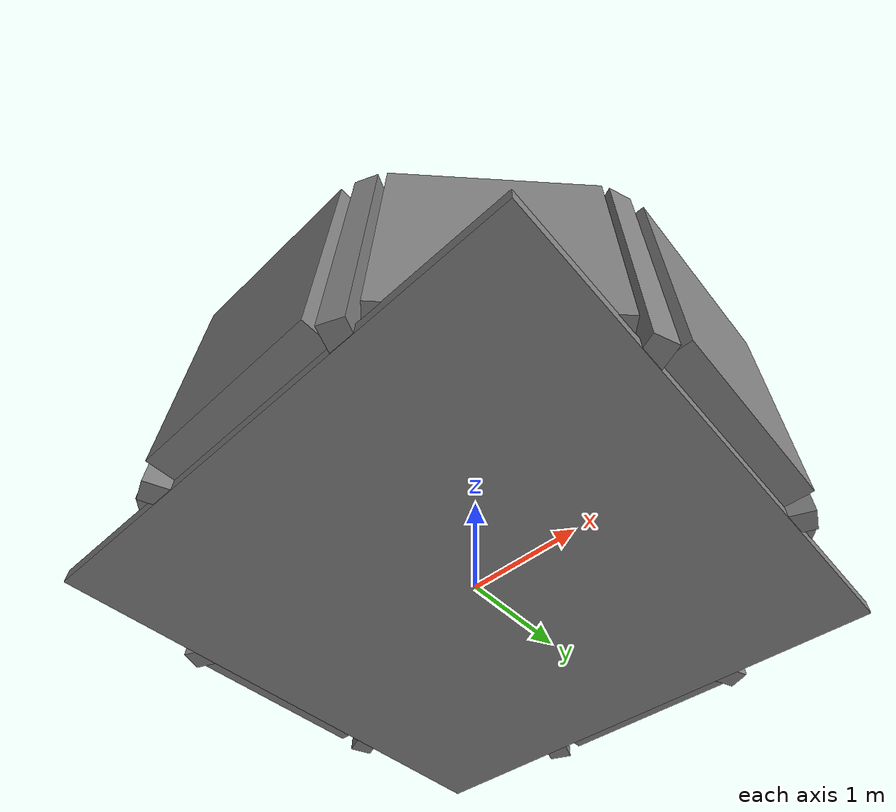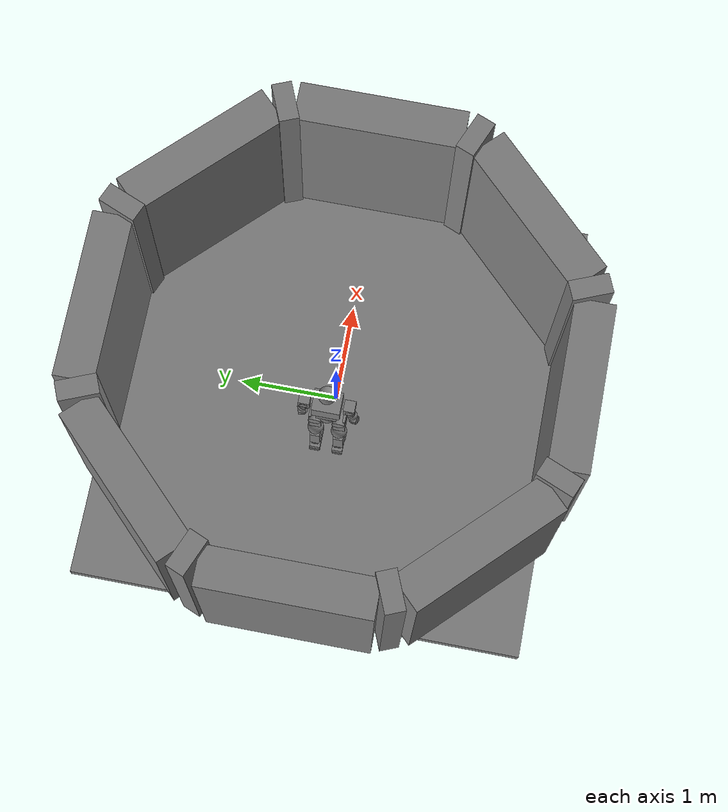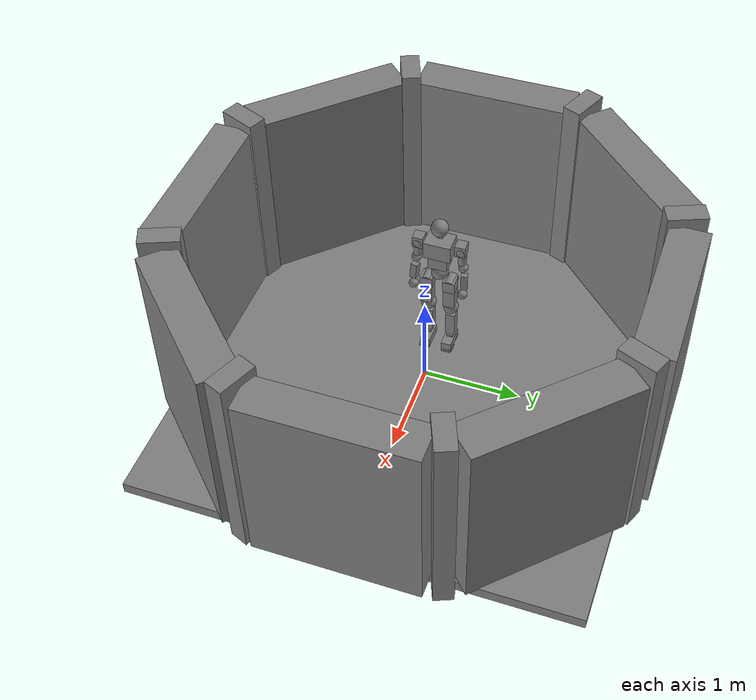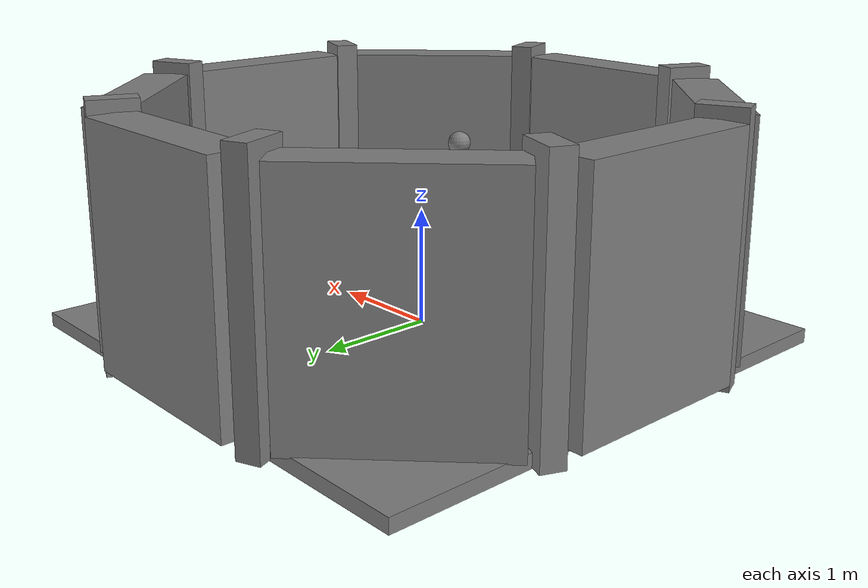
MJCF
<?xml version='1.0' encoding='utf-8'?>
<mujoco model="rek_LINK_BASE_3177_arena">
  <compiler coordinate="local" />
  <option timestep="0.019999992913832199" gravity="0 0 -9.8100004196166992" impratio="1" magnetic="0 0 0" wind="0 0 0" density="0" viscosity="0" o_margin="0" o_solref="0.019999999552965164 1" o_solimp="0.89999997615814209 0.94999998807907104 0.0010000000474974513 0.5 2" integrator="implicitfast" cone="elliptic" jacobian="auto" solver="Newton" iterations="100" tolerance="9.9999999392252903e-09" noslip_iterations="0" noslip_tolerance="9.9999999747524271e-07" ccd_iterations="50" ccd_tolerance="9.9999999747524271e-07">
    <flag constraint="enable" equality="enable" frictionloss="enable" limit="enable" contact="enable" spring="enable" damper="enable" gravity="enable" clampctrl="enable" warmstart="enable" filterparent="enable" actuation="enable" refsafe="enable" override="disable" energy="disable" fwdinv="disable" multiccd="disable" />
  </option>
  <size memory="-1" />
  <custom />
  <worldbody>
    <geom name="arena_Collider_Floor_Rektagon" type="box" pos="0 0 -0.05000000074505806" quat="-0.70710678118654757 0 0 0.70710678118654757" size="2.2999999523162837 2.2999999523162837 0.059999998658895493" priority="0" contype="2" conaffinity="1" group="0" condim="3" solmix="1" solref="0.019999999552965164 1" solimp="0.89999997615814209 0.94999998807907104 0.0010000000474974513" margin="0" gap="0" friction="1 0.004999999888241291 9.9999997473787516e-05" fluidshape="none" fluidcoef="5 0.25 1.5 1 1" />
    <geom name="arena_Collider_Pillar_01" type="box" pos="2.2635049557696094 -0.93757428978008317 1" quat="-0.55557025832218543 0 0 0.83146959539589904" size="0.10000000149011609 0.20000000298023218 1.1000000238418579" priority="0" contype="2" conaffinity="1" group="0" condim="3" solmix="1" solref="0.019999999552965164 1" solimp="0.89999997615814209 0.94999998807907104 0.0010000000474974513" margin="0" gap="0" friction="1 0.004999999888241291 9.9999997473787516e-05" fluidshape="none" fluidcoef="5 0.25 1.5 1 1" />
    <geom name="arena_Collider_Pillar_02" type="box" pos="2.2635049557696085 0.93757428978008417 1" quat="-0.83146959539589904 0 0 0.55557025832218543" size="0.10000000149011609 0.20000000298023218 1.1000000238418579" priority="0" contype="2" conaffinity="1" group="0" condim="3" solmix="1" solref="0.019999999552965164 1" solimp="0.89999997615814209 0.94999998807907104 0.0010000000474974513" margin="0" gap="0" friction="1 0.004999999888241291 9.9999997473787516e-05" fluidshape="none" fluidcoef="5 0.25 1.5 1 1" />
    <geom name="arena_Collider_Pillar_03" type="box" pos="0.93757486498700593 2.2635047175110561 1" quat="-0.98078526155165546 0 0 0.19509041678937211" size="0.10000000149011611 0.20000000298023221 1.1000000238418579" priority="0" contype="2" conaffinity="1" group="0" condim="3" solmix="1" solref="0.019999999552965164 1" solimp="0.89999997615814209 0.94999998807907104 0.0010000000474974513" margin="0" gap="0" friction="1 0.004999999888241291 9.9999997473787516e-05" fluidshape="none" fluidcoef="5 0.25 1.5 1 1" />
    <geom name="arena_Collider_Pillar_04" type="box" pos="-0.93757449072096111 2.263504872537176 1" quat="-0.98078527768055968 0 0 -0.1950903357039187" size="0.10000000149011609 0.20000000298023218 1.1000000238418579" priority="0" contype="2" conaffinity="1" group="0" condim="3" solmix="1" solref="0.019999999552965164 1" solimp="0.89999997615814209 0.94999998807907104 0.0010000000474974513" margin="0" gap="0" friction="1 0.004999999888241291 9.9999997473787516e-05" fluidshape="none" fluidcoef="5 0.25 1.5 1 1" />
    <geom name="arena_Collider_Pillar_05" type="box" pos="-2.263504802540059 0.93757465970891984 1" quat="-0.83146964079483965 0 0 -0.55557019037786803" size="0.10000000149011609 0.20000000298023218 1.1000000238418579" priority="0" contype="2" conaffinity="1" group="0" condim="3" solmix="1" solref="0.019999999552965164 1" solimp="0.89999997615814209 0.94999998807907104 0.0010000000474974513" margin="0" gap="0" friction="1 0.004999999888241291 9.9999997473787516e-05" fluidshape="none" fluidcoef="5 0.25 1.5 1 1" />
    <geom name="arena_Collider_Pillar_06" type="box" pos="-2.2635049557696094 -0.93757428978008417 1" quat="-0.55557025832218543 0 0 -0.83146959539589904" size="0.10000000149011612 0.20000000298023224 1.1000000238418579" priority="0" contype="2" conaffinity="1" group="0" condim="3" solmix="1" solref="0.019999999552965164 1" solimp="0.89999997615814209 0.94999998807907104 0.0010000000474974513" margin="0" gap="0" friction="1 0.004999999888241291 9.9999997473787516e-05" fluidshape="none" fluidcoef="5 0.25 1.5 1 1" />
    <geom name="arena_Collider_Pillar_07" type="box" pos="-0.93757546360911292 -2.2635044695534319 1" quat="-0.19509054648200319 0 0 -0.98078523575416532" size="0.10000000149011609 0.20000000298023218 1.1000000238418579" priority="0" contype="2" conaffinity="1" group="0" condim="3" solmix="1" solref="0.019999999552965164 1" solimp="0.89999997615814209 0.94999998807907104 0.0010000000474974513" margin="0" gap="0" friction="1 0.004999999888241291 9.9999997473787516e-05" fluidshape="none" fluidcoef="5 0.25 1.5 1 1" />
    <geom name="arena_Collider_Pillar_08" type="box" pos="0.93757486498700704 -2.2635047175110556 1" quat="0.19509041678937211 0 0 -0.98078526155165546" size="0.10000000149011609 0.20000000298023218 1.1000000238418579" priority="0" contype="2" conaffinity="1" group="0" condim="3" solmix="1" solref="0.019999999552965164 1" solimp="0.89999997615814209 0.94999998807907104 0.0010000000474974513" margin="0" gap="0" friction="1 0.004999999888241291 9.9999997473787516e-05" fluidshape="none" fluidcoef="5 0.25 1.5 1 1" />
    <geom name="arena_Collider_Wall_01" type="box" pos="2.3399999141693111 5.1958435646633195e-16 1" quat="-0.70710678118654757 0 0 0.70710678118654757" size="0.83999997377395608 0.20000000298023218 1" priority="0" contype="2" conaffinity="1" group="0" condim="3" solmix="1" solref="0.019999999552965164 1" solimp="0.89999997615814209 0.94999998807907104 0.0010000000474974513" margin="0" gap="0" friction="1 0.004999999888241291 9.9999997473787516e-05" fluidshape="none" fluidcoef="5 0.25 1.5 1 1" />
    <geom name="arena_Collider_Wall_02" type="box" pos="1.6546306547274046 1.6546289598422794 1" quat="-0.92387943451283194 0 0 0.38268366895420286" size="0.83999997377395608 0.20000000298023218 1" priority="0" contype="2" conaffinity="1" group="0" condim="3" solmix="1" solref="0.019999999552965164 1" solimp="0.89999997615814209 0.94999998807907104 0.0010000000474974513" margin="0" gap="0" friction="1 0.004999999888241291 9.9999997473787516e-05" fluidshape="none" fluidcoef="5 0.25 1.5 1 1" />
    <geom name="arena_Collider_Wall_03" type="box" pos="1.1834834827893186e-06 2.3399999141690113 1" quat="-0.99999999999996803 0 0 2.5288109539722825e-07" size="0.83999997377395597 0.20000000298023218 1" priority="0" contype="2" conaffinity="1" group="0" condim="3" solmix="1" solref="0.019999999552965164 1" solimp="0.89999997615814209 0.94999998807907104 0.0010000000474974513" margin="0" gap="0" friction="1 0.004999999888241291 9.9999997473787516e-05" fluidshape="none" fluidcoef="5 0.25 1.5 1 1" />
    <geom name="arena_Collider_Wall_04" type="box" pos="-1.6546288949328962 1.6546307196367194 1" quat="-0.92387963801580608 0 0 -0.3826831776545489" size="0.8399999737739563 0.20000000298023224 1" priority="0" contype="2" conaffinity="1" group="0" condim="3" solmix="1" solref="0.019999999552965164 1" solimp="0.89999997615814209 0.94999998807907104 0.0010000000474974513" margin="0" gap="0" friction="1 0.004999999888241291 9.9999997473787516e-05" fluidshape="none" fluidcoef="5 0.25 1.5 1 1" />
    <geom name="arena_Collider_Wall_05" type="box" pos="-2.3399999141681804 2.3013349838180236e-06 1" quat="-0.70710712889792215 0 0 -0.70710643347500202" size="0.83999997377395652 0.20000000298023229 1" priority="0" contype="2" conaffinity="1" group="0" condim="3" solmix="1" solref="0.019999999552965164 1" solimp="0.89999997615814209 0.94999998807907104 0.0010000000474974513" margin="0" gap="0" friction="1 0.004999999888241291 9.9999997473787516e-05" fluidshape="none" fluidcoef="5 0.25 1.5 1 1" />
    <geom name="arena_Collider_Wall_06" type="box" pos="-1.6546316413733664 -1.6546279731947187 1" quat="-0.38268394440632869 0 0 -0.92387932041669496" size="0.83999997377395608 0.20000000298023218 1" priority="0" contype="2" conaffinity="1" group="0" condim="3" solmix="1" solref="0.019999999552965164 1" solimp="0.89999997615814209 0.94999998807907104 0.0010000000474974513" margin="0" gap="0" friction="1 0.004999999888241291 9.9999997473787516e-05" fluidshape="none" fluidcoef="5 0.25 1.5 1 1" />
    <geom name="arena_Collider_Wall_07" type="box" pos="-3.7476975373293713e-06 -2.3399999141663095 1" quat="-8.0079010156275388e-07 0 0 -0.99999999999967937" size="0.83999997377395597 0.20000000298023218 1" priority="0" contype="2" conaffinity="1" group="0" condim="3" solmix="1" solref="0.019999999552965164 1" solimp="0.89999997615814209 0.94999998807907104 0.0010000000474974513" margin="0" gap="0" friction="1 0.004999999888241291 9.9999997473787516e-05" fluidshape="none" fluidcoef="5 0.25 1.5 1 1" />
    <geom name="arena_Collider_Wall_08" type="box" pos="1.6546254351887162 -1.6546341793698496 1" quat="0.38268221176393891 0 0 -0.92388003809989316" size="0.8399999737739563 0.20000000298023224 1" priority="0" contype="2" conaffinity="1" group="0" condim="3" solmix="1" solref="0.019999999552965164 1" solimp="0.89999997615814209 0.94999998807907104 0.0010000000474974513" margin="0" gap="0" friction="1 0.004999999888241291 9.9999997473787516e-05" fluidshape="none" fluidcoef="5 0.25 1.5 1 1" />
    <body name="LINK_BASE_3177" pos="-0.4574199914932251 -0.0028800000436604023 1.0399999711662531" quat="1 0 0 0" gravcomp="0">
      <body name="LINK_HIP_PITCH_L_3427" pos="0 0.079177998006343842 0" quat="1 0 0 0" gravcomp="0">
        <body name="LINK_HIP_ROLL_L_3210" pos="0.0046620001085102558 0.040321998298168182 -0.10751999914646149" quat="1 0 0 0" gravcomp="0">
          <body name="LINK_HIP_YAW_L_3255" pos="0.0094616003334522247 0 -0.080512002110481262" quat="1 0 0 0" gravcomp="0">
            <body name="LINK_KNEE_PITCH_L_3453" pos="-0.037707000970840454 0 -0.28791999816894531" quat="1 0 0 0" gravcomp="0">
              <body name="LINK_ANKLE_PITCH_L_3480" pos="-0.0027167999651283026 0 -0.43867000937461853" quat="1 0 0 0" gravcomp="0">
                <body name="LINK_ANKLE_ROLL_L_3193" pos="0.0011073000496253371 0 -0.037928000092506409" quat="1 0 0 0" gravcomp="0">
                  <body name="LINK_FOOT_L_3022" pos="0 0 0" quat="1 0 0 0" gravcomp="0">
                    <inertial pos="0 0 0" quat="1 0 0 0" mass="0.0010000000474974513" diaginertia="9.999999960041972e-13 9.999999960041972e-13 9.999999960041972e-13" />
                    <geom name="mjgeom_authored_3241" density="0" type="box" size="0.057000000029802322 0.054999999701976776 0.0099999997764825821" pos="0.10000000149011612 0.0016599999507889152 -0.054000001400709152" quat="1 0 0 0" priority="0" contype="1" conaffinity="1" group="0" condim="3" solmix="1" solref="0.019999999552965164 1" solimp="0.89999997615814209 0.94999998807907104 0.0010000000474974513" margin="0" gap="0" friction="1 0.004999999888241291 9.9999997473787516e-05" fluidshape="none" fluidcoef="5 0.25 1.5 1 1" />
                    <geom name="mjgeom_authored_3395" density="0" type="box" size="0.029999999329447746 0.05000000074505806 0.0099999997764825821" pos="-0.05299999937415123 0.0016599999507889152 -0.054000001400709152" quat="1 0 0 0" priority="0" contype="1" conaffinity="1" group="0" condim="3" solmix="1" solref="0.019999999552965164 1" solimp="0.89999997615814209 0.94999998807907104 0.0010000000474974513" margin="0" gap="0" friction="1 0.004999999888241291 9.9999997473787516e-05" fluidshape="none" fluidcoef="5 0.25 1.5 1 1" />
                    <geom name="mjgeom_authored_2931" density="0" type="box" size="0.017999999225139614 0.05000000074505806 0.0099999997764825804" pos="-0.092000000178813934 0.0016599999507889152 -0.045000001788139343" quat="0.9563826269454565 0 0.29211687879495735 0" priority="0" contype="1" conaffinity="1" group="0" condim="3" solmix="1" solref="0.019999999552965164 1" solimp="0.89999997615814209 0.94999998807907104 0.0010000000474974513" margin="0" gap="0" friction="1 0.004999999888241291 9.9999997473787516e-05" fluidshape="none" fluidcoef="5 0.25 1.5 1 1" />
                  </body>
                  <inertial pos="-0.0012873800005763769 -0.0012063799658790231 -0.022955799475312233" quat="0.46213480009613783 0.54236178627193277 0.55963580806756663 0.42318185412489384" mass="1.4943900108337402" diaginertia="0.0070707299746572971 0.0069149001501500607 0.0020277400035411119" />
                  <joint name="joint__J05_ANKLE_ROLL_L_3431" type="hinge" pos="0 0 0" axis="1 0 0" armature="0.035462498664855957" springref="0" springdamper="0 0" damping="0" stiffness="0" solreflimit="0.019999999552965164 1" solimplimit="0.89999997615814209 0.94999998807907104 0.0010000000474974513 0.5 2" solreffriction="0.019999999552965164 1" solimpfriction="0.89999997615814209 0.94999998807907104 0.0010000000474974513 0.5 2" frictionloss="0" limited="true" margin="0" range="-20.001956939697266 9.9981136322021484" ref="0" />
                  <geom name="mjgeom_3424" density="0" type="box" size="0.12126479996368292 0.050415162695571794 0.053187139565125115" pos="0.021552437916398048 -0.0035329684615135193 -0.010564938187599182" quat="3.0908621139995618e-08 3.0908621139995618e-08 -0.70710678118654691 -0.70710678118654691" priority="0" contype="1" conaffinity="2" group="0" condim="3" solmix="1" solref="0.019999999552965164 1" solimp="0.89999997615814209 0.94999998807907104 0.0010000000474974513" margin="0" gap="0" friction="1 0.004999999888241291 9.9999997473787516e-05" fluidshape="none" fluidcoef="5 0.25 1.5 1 1" />
                </body>
                <inertial pos="-3.6779998481506482e-05 0 -0.0088703297078609467" quat="0.70702695848104491 -0.010624499096089172 -0.010624499096089172 0.70702695848104491" mass="0.1442209929227829" diaginertia="8.4929997683502734e-05 6.7876797402277589e-05 3.8243200833676383e-05" />
                <joint name="joint__J04_ANKLE_PITCH_L_3132" type="hinge" pos="0 0 0" axis="-2.2204460492503126e-16 1 0" armature="0.035462498664855957" springref="0" springdamper="0 0" damping="0" stiffness="0" solreflimit="0.019999999552965164 1" solimplimit="0.89999997615814209 0.94999998807907104 0.0010000000474974513 0.5 2" solreffriction="0.019999999552965164 1" solimpfriction="0.89999997615814209 0.94999998807907104 0.0010000000474974513 0.5 2" frictionloss="0" limited="true" margin="0" range="-39.000091552734375 39.000091552734375" ref="0" />
                <geom name="mjgeom_3280" density="0" type="box" size="0.04818098095711322 0.032786364317871637 0.033811354660429067" pos="-0.017856383696198463 -0.00027835369110107422 -0.012690454721450806" quat="3.0908621139995618e-08 3.0908621139995618e-08 -0.70710678118654691 -0.70710678118654691" priority="0" contype="1" conaffinity="2" group="0" condim="3" solmix="1" solref="0.019999999552965164 1" solimp="0.89999997615814209 0.94999998807907104 0.0010000000474974513" margin="0" gap="0" friction="1 0.004999999888241291 9.9999997473787516e-05" fluidshape="none" fluidcoef="5 0.25 1.5 1 1" />
              </body>
              <inertial pos="-0.019744899123907089 0.0013916200259700418 -0.21190699934959412" quat="0.47545387451589743 0.021036093661089075 0.016898896229069427 0.87932674432064351" mass="5.9950299263000488" diaginertia="0.085845403373241425 0.085651099681854248 0.011571500450372696" />
              <joint name="joint__J03_KNEE_PITCH_L_3448" type="hinge" pos="0 0 0" axis="-2.2204460492503126e-16 1 0" armature="0.2427264004945755" springref="0" springdamper="0 0" damping="0" stiffness="0" solreflimit="0.019999999552965164 1" solimplimit="0.89999997615814209 0.94999998807907104 0.0010000000474974513 0.5 2" solreffriction="0.019999999552965164 1" solimpfriction="0.89999997615814209 0.94999998807907104 0.0010000000474974513 0.5 2" frictionloss="0" limited="true" margin="0" range="-14.992415428161621 134.93156433105469" ref="0" />
              <geom name="mjgeom_authored_2981" density="0" type="sphere" size="0.079999998211860657" pos="0 0 0" quat="1 0 0 0" priority="0" contype="1" conaffinity="1" group="0" condim="3" solmix="1" solref="0.019999999552965164 1" solimp="0.89999997615814209 0.94999998807907104 0.0010000000474974513" margin="0" gap="0" friction="1 0.004999999888241291 9.9999997473787516e-05" fluidshape="none" fluidcoef="5 0.25 1.5 1 1" />
              <geom name="mjgeom_authored_3148" density="0" type="box" size="0.05000000074505806 0.05000000074505806 0.14000000059604645" pos="-0.019999999552965164 0 -0.25" quat="1 0 0 0" priority="0" contype="1" conaffinity="1" group="0" condim="3" solmix="1" solref="0.019999999552965164 1" solimp="0.89999997615814209 0.94999998807907104 0.0010000000474974513" margin="0" gap="0" friction="1 0.004999999888241291 9.9999997473787516e-05" fluidshape="none" fluidcoef="5 0.25 1.5 1 1" />
            </body>
            <inertial pos="-0.018298400565981865 0.0023612300865352154 -0.17634700238704681" quat="0.70917573331364325 0.058818773489761889 0.04620788409111385 0.7010527530878391" mass="7.1948199272155762" diaginertia="0.11565600335597992 0.11401999741792679 0.010776599869132042" />
            <joint name="joint__J02_HIP_YAW_L_3403" type="hinge" pos="0 0 0" axis="-2.2204460492503126e-16 0 1" armature="0.044873699545860291" springref="0" springdamper="0 0" damping="0" stiffness="0" solreflimit="0.019999999552965164 1" solimplimit="0.89999997615814209 0.94999998807907104 0.0010000000474974513 0.5 2" solreffriction="0.019999999552965164 1" solimpfriction="0.89999997615814209 0.94999998807907104 0.0010000000474974513 0.5 2" frictionloss="0" limited="true" margin="0" range="-81.500381469726562 206.39543151855469" ref="0" />
            <geom name="mjgeom_authored_3473" density="0" type="box" size="0.059999998658895493 0.059999998658895493 0.10999999940395355" pos="0 0.0020000000949949026 -0.10000000149011612" quat="1 0 0 0" priority="0" contype="1" conaffinity="1" group="0" condim="3" solmix="1" solref="0.019999999552965164 1" solimp="0.89999997615814209 0.94999998807907104 0.0010000000474974513" margin="0" gap="0" friction="1 0.004999999888241291 9.9999997473787516e-05" fluidshape="none" fluidcoef="5 0.25 1.5 1 1" />
          </body>
          <inertial pos="0.037530899047851562 4.9499999477120582e-06 -0.034845501184463501" quat="0.9541172936490564 -3.7655712020968035e-05 0.29943309203351076 -0.00010925703093716646" mass="0.85144197940826416" diaginertia="0.0029199400451034307 0.0025723699945956469 0.0014565000310540199" />
          <joint name="joint__J01_HIP_ROLL_L_3156" type="hinge" pos="0 0 0" axis="1 0 0" armature="0.14110848307609558" springref="0" springdamper="0 0" damping="0" stiffness="0" solreflimit="0.019999999552965164 1" solimplimit="0.89999997615814209 0.94999998807907104 0.0010000000474974513 0.5 2" solreffriction="0.019999999552965164 1" solimpfriction="0.89999997615814209 0.94999998807907104 0.0010000000474974513 0.5 2" frictionloss="0" limited="true" margin="0" range="-61.994033813476562 117.97201538085938" ref="0" />
          <geom name="mjgeom_3095" density="0" type="box" size="0.065747229382395758 0.064645917154848589 0.063737563323229565" pos="0.01204218901693821 3.1255185604095459e-05 -0.00810222327709198" quat="3.0908621139995618e-08 3.0908621139995618e-08 -0.70710678118654691 -0.70710678118654691" priority="0" contype="1" conaffinity="2" group="0" condim="3" solmix="1" solref="0.019999999552965164 1" solimp="0.89999997615814209 0.94999998807907104 0.0010000000474974513" margin="0" gap="0" friction="1 0.004999999888241291 9.9999997473787516e-05" fluidshape="none" fluidcoef="5 0.25 1.5 1 1" />
        </body>
        <inertial pos="0.0061913998797535896 0.039193999022245407 -0.098997600376605988" quat="0.7030482939990742 -0.00094050239532821435 -0.083500140030117881 0.70622230096138028" mass="3.5361900329589844" diaginertia="0.0079573197290301323 0.0071615199558436871 0.0047642500139772892" />
        <joint name="joint__J00_HIP_PITCH_L_3202" type="hinge" pos="0 0 0" axis="-2.8001219565254587e-08 0.96592584692892935 -0.25881896807349691" armature="0.2427264004945755" springref="0" springdamper="0 0" damping="0" stiffness="0" solreflimit="0.019999999552965164 1" solimplimit="0.89999997615814209 0.94999998807907104 0.0010000000474974513 0.5 2" solreffriction="0.019999999552965164 1" solimpfriction="0.89999997615814209 0.94999998807907104 0.0010000000474974513 0.5 2" frictionloss="0" limited="true" margin="0" range="-189.99281311035156 130.00413513183594" ref="0" />
        <geom name="mjgeom_authored_3004" density="0" type="cylinder" size="0.061999998986721025 0.079999998211860643" pos="0 0.039999999105930328 -0.10000000149011612" quat="0.70710678118654757 0 0.70710678118654757 0" priority="0" contype="1" conaffinity="1" group="0" condim="3" solmix="1" solref="0.019999999552965164 1" solimp="0.89999997615814209 0.94999998807907104 0.0010000000474974513" margin="0" gap="0" friction="1 0.004999999888241291 9.9999997473787516e-05" fluidshape="none" fluidcoef="5 0.25 1.5 1 1" />
      </body>
      <body name="LINK_HIP_PITCH_R_3313" pos="0 -0.079177998006343842 0" quat="1 0 0 0" gravcomp="0">
        <body name="LINK_HIP_ROLL_R_3154" pos="0.0046620001085102558 -0.040321998298168182 -0.10751999914646149" quat="1 0 0 0" gravcomp="0">
          <body name="LINK_HIP_YAW_R_3008" pos="0.0094616003334522247 0 -0.080512002110481262" quat="1 0 0 0" gravcomp="0">
            <body name="LINK_KNEE_PITCH_R_3054" pos="-0.037707000970840454 0 -0.28791999816894531" quat="1 0 0 0" gravcomp="0">
              <body name="LINK_ANKLE_PITCH_R_3327" pos="-0.0027167999651283026 0 -0.43867000937461853" quat="1 0 0 0" gravcomp="0">
                <body name="LINK_ANKLE_ROLL_R_3212" pos="0.0011073000496253371 0 -0.037928000092506409" quat="1 0 0 0" gravcomp="0">
                  <body name="LINK_FOOT_R_2916" pos="0 0 0" quat="1 0 0 0" gravcomp="0">
                    <inertial pos="0 0 0" quat="1 0 0 0" mass="0.0010000000474974513" diaginertia="9.999999960041972e-13 9.999999960041972e-13 9.999999960041972e-13" />
                    <geom name="mjgeom_authored_3121" density="0" type="box" size="0.057000000029802322 0.054999999701976776 0.0099999997764825821" pos="0.10000000149011612 -0.0016599999507889152 -0.054000001400709152" quat="1 0 0 0" priority="0" contype="1" conaffinity="1" group="0" condim="3" solmix="1" solref="0.019999999552965164 1" solimp="0.89999997615814209 0.94999998807907104 0.0010000000474974513" margin="0" gap="0" friction="1 0.004999999888241291 9.9999997473787516e-05" fluidshape="none" fluidcoef="5 0.25 1.5 1 1" />
                    <geom name="mjgeom_authored_3287" density="0" type="box" size="0.029999999329447746 0.05000000074505806 0.0099999997764825821" pos="-0.05299999937415123 0.0016599999507889152 -0.054000001400709152" quat="1 0 0 0" priority="0" contype="1" conaffinity="1" group="0" condim="3" solmix="1" solref="0.019999999552965164 1" solimp="0.89999997615814209 0.94999998807907104 0.0010000000474974513" margin="0" gap="0" friction="1 0.004999999888241291 9.9999997473787516e-05" fluidshape="none" fluidcoef="5 0.25 1.5 1 1" />
                    <geom name="mjgeom_authored_3014" density="0" type="box" size="0.017999999225139614 0.05000000074505806 0.0099999997764825804" pos="-0.092000000178813934 0.0016599999507889152 -0.045000001788139343" quat="0.9563826269454565 0 0.29211687879495735 0" priority="0" contype="1" conaffinity="1" group="0" condim="3" solmix="1" solref="0.019999999552965164 1" solimp="0.89999997615814209 0.94999998807907104 0.0010000000474974513" margin="0" gap="0" friction="1 0.004999999888241291 9.9999997473787516e-05" fluidshape="none" fluidcoef="5 0.25 1.5 1 1" />
                  </body>
                  <inertial pos="-0.0012873800005763769 0.0012063799658790231 -0.022955799475312233" quat="0.42318185412489384 0.55963580806756663 0.54236178627193277 0.46213480009613783" mass="1.4943900108337402" diaginertia="0.0070707299746572971 0.0069149001501500607 0.0020277400035411119" />
                  <joint name="joint__J11_ANKLE_ROLL_R_3208" type="hinge" pos="0 0 0" axis="1 0 0" armature="0.035462498664855957" springref="0" springdamper="0 0" damping="0" stiffness="0" solreflimit="0.019999999552965164 1" solimplimit="0.89999997615814209 0.94999998807907104 0.0010000000474974513 0.5 2" solreffriction="0.019999999552965164 1" solimpfriction="0.89999997615814209 0.94999998807907104 0.0010000000474974513 0.5 2" frictionloss="0" limited="true" margin="0" range="-9.9981136322021484 20.001956939697266" ref="0" />
                  <geom name="mjgeom_3140" density="0" type="box" size="0.12126479996368292 0.050415162695571794 0.053187145385891206" pos="0.021552443504333496 0.003597162663936615 -0.010564938187599182" quat="3.0908621139995618e-08 3.0908621139995618e-08 -0.70710678118654691 -0.70710678118654691" priority="0" contype="1" conaffinity="2" group="0" condim="3" solmix="1" solref="0.019999999552965164 1" solimp="0.89999997615814209 0.94999998807907104 0.0010000000474974513" margin="0" gap="0" friction="1 0.004999999888241291 9.9999997473787516e-05" fluidshape="none" fluidcoef="5 0.25 1.5 1 1" />
                </body>
                <inertial pos="-3.6779998481506482e-05 0 -0.0088703297078609467" quat="0.70702695848104491 -0.010624499096089172 -0.010624499096089172 0.70702695848104491" mass="0.1442209929227829" diaginertia="8.4929997683502734e-05 6.7876797402277589e-05 3.8243200833676383e-05" />
                <joint name="joint__J10_ANKLE_PITCH_R_3006" type="hinge" pos="0 0 0" axis="-2.2204460492503126e-16 1 0" armature="0.035462498664855957" springref="0" springdamper="0 0" damping="0" stiffness="0" solreflimit="0.019999999552965164 1" solimplimit="0.89999997615814209 0.94999998807907104 0.0010000000474974513 0.5 2" solreffriction="0.019999999552965164 1" solimpfriction="0.89999997615814209 0.94999998807907104 0.0010000000474974513 0.5 2" frictionloss="0" limited="true" margin="0" range="-39.000091552734375 39.000091552734375" ref="0" />
                <geom name="mjgeom_3102" density="0" type="box" size="0.04818098095711322 0.032786364317871637 0.033811354660429067" pos="-0.017856383696198463 0.00034254789352416992 -0.012690454721450806" quat="3.0908621139995618e-08 3.0908621139995618e-08 -0.70710678118654691 -0.70710678118654691" priority="0" contype="1" conaffinity="2" group="0" condim="3" solmix="1" solref="0.019999999552965164 1" solimp="0.89999997615814209 0.94999998807907104 0.0010000000474974513" margin="0" gap="0" friction="1 0.004999999888241291 9.9999997473787516e-05" fluidshape="none" fluidcoef="5 0.25 1.5 1 1" />
              </body>
              <inertial pos="-0.019744899123907089 -0.0013916200259700418 -0.21190699934959412" quat="0.87932674432064351 0.016898896229069427 0.021036093661089075 0.47545387451589743" mass="5.9950299263000488" diaginertia="0.085845403373241425 0.085651099681854248 0.011571500450372696" />
              <joint name="joint__J09_KNEE_PITCH_R_3252" type="hinge" pos="0 0 0" axis="-2.2204460492503126e-16 1 0" armature="0.2427264004945755" springref="0" springdamper="0 0" damping="0" stiffness="0" solreflimit="0.019999999552965164 1" solimplimit="0.89999997615814209 0.94999998807907104 0.0010000000474974513 0.5 2" solreffriction="0.019999999552965164 1" solimpfriction="0.89999997615814209 0.94999998807907104 0.0010000000474974513 0.5 2" frictionloss="0" limited="true" margin="0" range="-14.992415428161621 134.93156433105469" ref="0" />
              <geom name="mjgeom_authored_3088" density="0" type="sphere" size="0.079999998211860657" pos="0 0 0" quat="1 0 0 0" priority="0" contype="1" conaffinity="1" group="0" condim="3" solmix="1" solref="0.019999999552965164 1" solimp="0.89999997615814209 0.94999998807907104 0.0010000000474974513" margin="0" gap="0" friction="1 0.004999999888241291 9.9999997473787516e-05" fluidshape="none" fluidcoef="5 0.25 1.5 1 1" />
              <geom name="mjgeom_authored_3029" density="0" type="box" size="0.05000000074505806 0.05000000074505806 0.14000000059604645" pos="-0.019999999552965164 0 -0.25" quat="1 0 0 0" priority="0" contype="1" conaffinity="1" group="0" condim="3" solmix="1" solref="0.019999999552965164 1" solimp="0.89999997615814209 0.94999998807907104 0.0010000000474974513" margin="0" gap="0" friction="1 0.004999999888241291 9.9999997473787516e-05" fluidshape="none" fluidcoef="5 0.25 1.5 1 1" />
            </body>
            <inertial pos="-0.018298400565981865 -0.0023612300865352154 -0.17634700238704681" quat="0.7010527530878391 0.04620788409111385 0.058818773489761889 0.70917573331364325" mass="7.1948199272155762" diaginertia="0.11565600335597992 0.11401999741792679 0.010776599869132042" />
            <joint name="joint__J08_HIP_YAW_R_3013" type="hinge" pos="0 0 0" axis="-2.2204460492503126e-16 0 1" armature="0.044873699545860291" springref="0" springdamper="0 0" damping="0" stiffness="0" solreflimit="0.019999999552965164 1" solimplimit="0.89999997615814209 0.94999998807907104 0.0010000000474974513 0.5 2" solreffriction="0.019999999552965164 1" solimpfriction="0.89999997615814209 0.94999998807907104 0.0010000000474974513 0.5 2" frictionloss="0" limited="true" margin="0" range="-206.39543151855469 81.500381469726562" ref="0" />
            <geom name="mjgeom_authored_2989" density="0" type="box" size="0.059999998658895493 0.059999998658895493 0.10999999940395355" pos="0 -0.0020000000949949026 -0.10000000149011612" quat="1 0 0 0" priority="0" contype="1" conaffinity="1" group="0" condim="3" solmix="1" solref="0.019999999552965164 1" solimp="0.89999997615814209 0.94999998807907104 0.0010000000474974513" margin="0" gap="0" friction="1 0.004999999888241291 9.9999997473787516e-05" fluidshape="none" fluidcoef="5 0.25 1.5 1 1" />
          </body>
          <inertial pos="0.037530899047851562 -4.9499999477120582e-06 -0.034845501184463501" quat="0.9541172936490564 3.7655712020968035e-05 0.29943309203351076 0.00010925703093716646" mass="0.85144197940826416" diaginertia="0.0029199400451034307 0.0025723699945956469 0.0014565000310540199" />
          <joint name="joint__J07_HIP_ROLL_R_2962" type="hinge" pos="0 0 0" axis="1 0 0" armature="0.14110848307609558" springref="0" springdamper="0 0" damping="0" stiffness="0" solreflimit="0.019999999552965164 1" solimplimit="0.89999997615814209 0.94999998807907104 0.0010000000474974513 0.5 2" solreffriction="0.019999999552965164 1" solimpfriction="0.89999997615814209 0.94999998807907104 0.0010000000474974513 0.5 2" frictionloss="0" limited="true" margin="0" range="-117.97201538085938 61.994033813476562" ref="0" />
          <geom name="mjgeom_3326" density="0" type="box" size="0.065747229382395758 0.064645917154848589 0.063737563323229565" pos="0.01204218901693821 3.2916665077209473e-05 -0.00810222327709198" quat="3.0908621139995618e-08 3.0908621139995618e-08 -0.70710678118654691 -0.70710678118654691" priority="0" contype="1" conaffinity="2" group="0" condim="3" solmix="1" solref="0.019999999552965164 1" solimp="0.89999997615814209 0.94999998807907104 0.0010000000474974513" margin="0" gap="0" friction="1 0.004999999888241291 9.9999997473787516e-05" fluidshape="none" fluidcoef="5 0.25 1.5 1 1" />
        </body>
        <inertial pos="0.0061913998797535896 -0.039193999022245407 -0.098997600376605988" quat="0.70622230096138028 -0.083500140030117881 -0.00094050239532821435 0.7030482939990742" mass="3.5361900329589844" diaginertia="0.0079573197290301323 0.0071615199558436871 0.0047642500139772892" />
        <joint name="joint__J06_HIP_PITCH_R_3167" type="hinge" pos="0 0 0" axis="-2.8001219565254587e-08 0.96592584692892935 0.25881896807349691" armature="0.2427264004945755" springref="0" springdamper="0 0" damping="0" stiffness="0" solreflimit="0.019999999552965164 1" solimplimit="0.89999997615814209 0.94999998807907104 0.0010000000474974513 0.5 2" solreffriction="0.019999999552965164 1" solimpfriction="0.89999997615814209 0.94999998807907104 0.0010000000474974513 0.5 2" frictionloss="0" limited="true" margin="0" range="-189.99281311035156 130.00413513183594" ref="0" />
        <geom name="mjgeom_authored_3333" density="0" type="cylinder" size="0.061999998986721025 0.079999998211860643" pos="0 -0.039999999105930328 -0.10000000149011612" quat="0.70710678118654757 0 0.70710678118654757 0" priority="0" contype="1" conaffinity="1" group="0" condim="3" solmix="1" solref="0.019999999552965164 1" solimp="0.89999997615814209 0.94999998807907104 0.0010000000474974513" margin="0" gap="0" friction="1 0.004999999888241291 9.9999997473787516e-05" fluidshape="none" fluidcoef="5 0.25 1.5 1 1" />
      </body>
      <body name="LINK_WAIST_YAW_3445" pos="0 0 0.10384000092744827" quat="1 0 0 0" gravcomp="0">
        <body name="LINK_HEAD_PITCH_3361" pos="-0.011300000362098217 0 0.38604000210762024" quat="1 0 0 0" gravcomp="0">
          <body name="LINK_HEAD_YAW_3342" pos="0 0 0.040199000388383865" quat="1 0 0 0" gravcomp="0">
            <inertial pos="0.018132599070668221 4.9199998102267273e-06 0.092894397675991058" quat="0.33815790055348249 0.6210657559784406 0.62132277119038937 0.33746788742706207" mass="1.7237700223922729" diaginertia="0.0084851300343871117 0.0082612903788685799 0.0065395999699831009" />
            <joint name="joint__J24_HEAD_YAW_3294" type="hinge" pos="0 0 0" axis="-2.2204460492503126e-16 0 1" armature="0.0067162499763071537" springref="0" springdamper="0 0" damping="0" stiffness="0" solreflimit="0.019999999552965164 1" solimplimit="0.89999997615814209 0.94999998807907104 0.0010000000474974513 0.5 2" solreffriction="0.019999999552965164 1" solimpfriction="0.89999997615814209 0.94999998807907104 0.0010000000474974513 0.5 2" frictionloss="0" limited="true" margin="0" range="-70.01544189453125 70.01544189453125" ref="0" />
            <geom name="mjgeom_authored_3125" density="0" type="sphere" size="0.090000003576278687" pos="0.017999999225139618 0 0.079999998211860657" quat="1 0 0 0" priority="0" contype="1" conaffinity="1" group="0" condim="3" solmix="1" solref="0.019999999552965164 1" solimp="0.89999997615814209 0.94999998807907104 0.0010000000474974513" margin="0" gap="0" friction="1 0.004999999888241291 9.9999997473787516e-05" fluidshape="none" fluidcoef="5 0.25 1.5 1 1" />
          </body>
          <inertial pos="0.00012688999413512647 0.00010014000145019963 0.067295297980308533" quat="0.99904520385077322 -0.043609304079558653 0.0015927501173754501 0.002091030254953434" mass="0.70796602964401245" diaginertia="0.00066047400468960404 0.00056427798699587584 0.00045508900075219572" />
          <joint name="joint__J23_HEAD_PITCH_3223" type="hinge" pos="0 0 0" axis="-2.2204460492503126e-16 1 0" armature="0.0067162499763071537" springref="0" springdamper="0 0" damping="0" stiffness="0" solreflimit="0.019999999552965164 1" solimplimit="0.89999997615814209 0.94999998807907104 0.0010000000474974513 0.5 2" solreffriction="0.019999999552965164 1" solimpfriction="0.89999997615814209 0.94999998807907104 0.0010000000474974513 0.5 2" frictionloss="0" limited="true" margin="0" range="-29.965692520141602 29.965692520141602" ref="0" />
          <geom name="mjgeom_2892" density="0" type="box" size="0.017814448801800612 0.017772120190784339 0.029249984072521332" pos="8.4945932030677795e-06 0.0010320888832211494 4.6819448471069336e-05" quat="3.0908621139995618e-08 3.0908621139995618e-08 -0.70710678118654691 -0.70710678118654691" priority="0" contype="1" conaffinity="2" group="0" condim="3" solmix="1" solref="0.019999999552965164 1" solimp="0.89999997615814209 0.94999998807907104 0.0010000000474974513" margin="0" gap="0" friction="1 0.004999999888241291 9.9999997473787516e-05" fluidshape="none" fluidcoef="5 0.25 1.5 1 1" />
        </body>
        <body name="LINK_SHOULDER_PITCH_L_3003" pos="-0.010999999940395355 0.1630299985408783 0.27889001369476318" quat="1 0 0 0" gravcomp="0">
          <body name="LINK_SHOULDER_ROLL_L_3396" pos="0 0.062532998621463776 -0.015455000102519989" quat="1 0 0 0" gravcomp="0">
            <body name="LINK_SHOULDER_YAW_L_3103" pos="3.4601998777361587e-05 0.0085246004164218903 -0.082712002098560333" quat="1 0 0 0" gravcomp="0">
              <body name="LINK_ELBOW_PITCH_L_3303" pos="0.0019251999910920858 0.013597000390291214 -0.15074999630451202" quat="1 0 0 0" gravcomp="0">
                <body name="LINK_ELBOW_YAW_L_3350" pos="-0.0022090999409556389 0.0094362003728747368 -0.13181999325752258" quat="1 0 0 0" gravcomp="0">
                  <body name="LINK_WRIST_END_L_2899" pos="0.029435999691486359 0.012485500425100327 -0.13222150504589081" quat="1 0 0 0" gravcomp="0">
                    <inertial pos="0 0 0" quat="1 0 0 0" mass="0.0010000000474974513" diaginertia="9.999999960041972e-13 9.999999960041972e-13 9.999999960041972e-13" />
                    <geom name="mjgeom_authored_3435" density="0" type="sphere" size="0.05000000074505806" pos="0.026000000536441803 -0.008999999612569809 -0.059999998658895493" quat="1 0 0 0" priority="0" contype="1" conaffinity="1" group="0" condim="3" solmix="1" solref="0.019999999552965164 1" solimp="0.89999997615814209 0.94999998807907104 0.0010000000474974513" margin="0" gap="0" friction="1 0.004999999888241291 9.9999997473787516e-05" fluidshape="none" fluidcoef="5 0.25 1.5 1 1" />
                  </body>
                  <inertial pos="0.013009400106966496 0.0044797500595450401 -0.05843840166926384" quat="0.70249378018499253 -0.045093483797508487 -0.10659295965016564 0.70221578412438257" mass="1.0788199901580811" diaginertia="0.0021501700393855572 0.0020166700705885887 0.00085407297592610121" />
                  <joint name="joint__J17_ELBOW_YAW_L_2903" type="hinge" pos="0 0 0" axis="-0.2164390775440248 -0.069802836083640601 0.97379756098820269" armature="0.0067162499763071537" springref="0" springdamper="0 0" damping="0" stiffness="0" solreflimit="0.019999999552965164 1" solimplimit="0.89999997615814209 0.94999998807907104 0.0010000000474974513 0.5 2" solreffriction="0.019999999552965164 1" solimpfriction="0.89999997615814209 0.94999998807907104 0.0010000000474974513 0.5 2" frictionloss="0" limited="true" margin="0" range="-150.00035095214844 150.00035095214844" ref="0" />
                  <geom name="mjgeom_authored_3317" density="0" type="box" size="0.035000000149011612 0.035000000149011612 0.079999998211860657" pos="0.014000000432133675 0.004999999888241291 -0.05000000074505806" quat="0.98763760366485664 0.010995965720700156 -0.086968088792974477 0.12995231470314833" priority="0" contype="1" conaffinity="1" group="0" condim="3" solmix="1" solref="0.019999999552965164 1" solimp="0.89999997615814209 0.94999998807907104 0.0010000000474974513" margin="0" gap="0" friction="1 0.004999999888241291 9.9999997473787516e-05" fluidshape="none" fluidcoef="5 0.25 1.5 1 1" />
                </body>
                <inertial pos="-0.0088349701836705208 0.0029520299285650253 -0.073333397507667542" quat="0.99291108459622723 0.086900404203694104 0.011758301220093704 0.080234906291438007" mass="1.1952699422836304" diaginertia="0.0031966699752956629 0.0031064599752426147 0.0012679300270974636" />
                <joint name="joint__J16_ELBOW_PITCH_L_3166" type="hinge" pos="0 0 0" axis="-3.4745579968742391e-08 0.99744080865796003 0.071497085421391382" armature="0.035462498664855957" springref="0" springdamper="0 0" damping="0" stiffness="0" solreflimit="0.019999999552965164 1" solimplimit="0.89999997615814209 0.94999998807907104 0.0010000000474974513 0.5 2" solreffriction="0.019999999552965164 1" solimpfriction="0.89999997615814209 0.94999998807907104 0.0010000000474974513 0.5 2" frictionloss="0" limited="true" margin="0" range="-130.9781494140625 15.011493682861328" ref="0" />
                <geom name="mjgeom_authored_3131" density="0" type="sphere" size="0.05000000074505806" pos="0 0 0" quat="1 0 0 0" priority="0" contype="1" conaffinity="1" group="0" condim="3" solmix="1" solref="0.019999999552965164 1" solimp="0.89999997615814209 0.94999998807907104 0.0010000000474974513" margin="0" gap="0" friction="1 0.004999999888241291 9.9999997473787516e-05" fluidshape="none" fluidcoef="5 0.25 1.5 1 1" />
              </body>
              <inertial pos="0.00062214001081883907 0.0055498098954558372 -0.08980560302734375" quat="0.70639874657327728 0.016014593710949585 -0.024756989022396956 0.70719971374606838" mass="2.5520200729370117" diaginertia="0.0099796103313565254 0.0098341898992657661 0.0011442500399425626" />
              <joint name="joint__J15_SHOULDER_YAW_L_3493" type="hinge" pos="0 0 0" axis="-1.1882354833403494e-07 -0.07149707941006149 0.9974408090888488" armature="0.035462498664855957" springref="0" springdamper="0 0" damping="0" stiffness="0" solreflimit="0.019999999552965164 1" solimplimit="0.89999997615814209 0.94999998807907104 0.0010000000474974513 0.5 2" solreffriction="0.019999999552965164 1" solimpfriction="0.89999997615814209 0.94999998807907104 0.0010000000474974513 0.5 2" frictionloss="0" limited="true" margin="0" range="-150.00035095214844 150.00035095214844" ref="0" />
              <geom name="mjgeom_authored_3471" density="0" type="cylinder" size="0.041999999433755875 0.059999998658895493" pos="0 0 -0.039999999105930328" quat="1 0 0 0" priority="0" contype="1" conaffinity="1" group="0" condim="3" solmix="1" solref="0.019999999552965164 1" solimp="0.89999997615814209 0.94999998807907104 0.0010000000474974513" margin="0" gap="0" friction="1 0.004999999888241291 9.9999997473787516e-05" fluidshape="none" fluidcoef="5 0.25 1.5 1 1" />
            </body>
            <inertial pos="-0.005571919959038496 0.0044665900059044361 -0.027129299938678741" quat="0.69930401648712981 -0.095837507317864903 -0.19685601406671516 0.6804680554161463" mass="0.68289297819137573" diaginertia="0.0021681899670511484 0.0015994500136002898 0.0014132000505924225" />
            <joint name="joint__J14_SHOULDER_ROLL_L_3297" type="hinge" pos="0 0 0" axis="1 0 0" armature="0.035462498664855957" springref="0" springdamper="0 0" damping="0" stiffness="0" solreflimit="0.019999999552965164 1" solimplimit="0.89999997615814209 0.94999998807907104 0.0010000000474974513 0.5 2" solreffriction="0.019999999552965164 1" solimpfriction="0.89999997615814209 0.94999998807907104 0.0010000000474974513 0.5 2" frictionloss="0" limited="true" margin="0" range="-22.001579284667969 139.97360229492188" ref="0" />
            <geom name="mjgeom_authored_2947" density="0" type="cylinder" size="0.041999999433755868 0.059999998658895479" pos="0 0 0" quat="0.70710678118654757 0 0.70710678118654757 0" priority="0" contype="1" conaffinity="1" group="0" condim="3" solmix="1" solref="0.019999999552965164 1" solimp="0.89999997615814209 0.94999998807907104 0.0010000000474974513" margin="0" gap="0" friction="1 0.004999999888241291 9.9999997473787516e-05" fluidshape="none" fluidcoef="5 0.25 1.5 1 1" />
          </body>
          <inertial pos="-0.0061545697972178459 0.052841801196336746 -0.012487100437283516" quat="0.83517465121690471 0.54769877707969339 0.028681288424544947 0.041069882449773221" mass="1.7688299417495728" diaginertia="0.0024097799323499203 0.0021395098883658648 0.0013071800349280238" />
          <joint name="joint__J13_SHOULDER_PITCH_L_3494" type="hinge" pos="0 0 0" axis="-3.6477507681098587e-09 0.99677888126457848 0.080198889424575745" armature="0.035462498664855957" springref="0" springdamper="0 0" damping="0" stiffness="0" solreflimit="0.019999999552965164 1" solimplimit="0.89999997615814209 0.94999998807907104 0.0010000000474974513 0.5 2" solreffriction="0.019999999552965164 1" solimpfriction="0.89999997615814209 0.94999998807907104 0.0010000000474974513 0.5 2" frictionloss="0" limited="true" margin="0" range="-169.99658203125 160.02711486816406" ref="0" />
          <geom name="mjgeom_2887" density="0" type="box" size="0.05838079960085453 0.063759268959984197 0.054950080811977393" pos="-0.00024313293397426605 0.057111412286758423 -0.0047956705093383789" quat="3.0908621139995618e-08 3.0908621139995618e-08 -0.70710678118654691 -0.70710678118654691" priority="0" contype="1" conaffinity="2" group="0" condim="3" solmix="1" solref="0.019999999552965164 1" solimp="0.89999997615814209 0.94999998807907104 0.0010000000474974513" margin="0" gap="0" friction="1 0.004999999888241291 9.9999997473787516e-05" fluidshape="none" fluidcoef="5 0.25 1.5 1 1" />
        </body>
        <body name="LINK_SHOULDER_PITCH_R_2901" pos="-0.010999999940395355 -0.1630299985408783 0.27889001369476318" quat="1 0 0 0" gravcomp="0">
          <body name="LINK_SHOULDER_ROLL_R_3243" pos="0 -0.062532998621463776 -0.015455000102519989" quat="1 0 0 0" gravcomp="0">
            <body name="LINK_SHOULDER_YAW_R_3325" pos="3.4601998777361587e-05 -0.0085246004164218903 -0.082712002098560333" quat="1 0 0 0" gravcomp="0">
              <body name="LINK_ELBOW_PITCH_R_3240" pos="0.0019251999910920858 -0.013597000390291214 -0.15074999630451202" quat="1 0 0 0" gravcomp="0">
                <body name="LINK_ELBOW_YAW_R_3286" pos="-0.0022090999409556389 -0.0094362003728747368 -0.13181999325752258" quat="1 0 0 0" gravcomp="0">
                  <body name="LINK_WRIST_END_R_3185" pos="0.029435999691486359 -0.012485500425100327 -0.13222150504589081" quat="1 0 0 0" gravcomp="0">
                    <inertial pos="0 0 0" quat="1 0 0 0" mass="0.0010000000474974513" diaginertia="9.999999960041972e-13 9.999999960041972e-13 9.999999960041972e-13" />
                    <geom name="mjgeom_authored_3197" density="0" type="sphere" size="0.05000000074505806" pos="0.026000000536441803 0.008999999612569809 -0.059999998658895493" quat="1 0 0 0" priority="0" contype="1" conaffinity="1" group="0" condim="3" solmix="1" solref="0.019999999552965164 1" solimp="0.89999997615814209 0.94999998807907104 0.0010000000474974513" margin="0" gap="0" friction="1 0.004999999888241291 9.9999997473787516e-05" fluidshape="none" fluidcoef="5 0.25 1.5 1 1" />
                  </body>
                  <inertial pos="0.013009400106966496 -0.0044797500595450401 -0.05843840166926384" quat="0.70221578412438257 -0.10659295965016564 -0.045093483797508487 0.70249378018499253" mass="1.0788199901580811" diaginertia="0.0021501700393855572 0.0020166700705885887 0.00085407297592610121" />
                  <joint name="joint__J22_ELBOW_YAW_R_3481" type="hinge" pos="0 0 0" axis="-0.2164390775440248 0.069802836083640601 0.97379756098820269" armature="0.0067162499763071537" springref="0" springdamper="0 0" damping="0" stiffness="0" solreflimit="0.019999999552965164 1" solimplimit="0.89999997615814209 0.94999998807907104 0.0010000000474974513 0.5 2" solreffriction="0.019999999552965164 1" solimpfriction="0.89999997615814209 0.94999998807907104 0.0010000000474974513 0.5 2" frictionloss="0" limited="true" margin="0" range="-150.00035095214844 150.00035095214844" ref="0" />
                  <geom name="mjgeom_authored_3344" density="0" type="box" size="0.035000000149011612 0.035000000149011612 0.079999998211860657" pos="0.014000000432133675 -0.004999999888241291 -0.05000000074505806" quat="0.98763760366485664 -0.010995965720700156 -0.086968088792974477 -0.12995231470314833" priority="0" contype="1" conaffinity="1" group="0" condim="3" solmix="1" solref="0.019999999552965164 1" solimp="0.89999997615814209 0.94999998807907104 0.0010000000474974513" margin="0" gap="0" friction="1 0.004999999888241291 9.9999997473787516e-05" fluidshape="none" fluidcoef="5 0.25 1.5 1 1" />
                </body>
                <inertial pos="-0.0088349701836705208 -0.0029520299285650253 -0.073333397507667542" quat="0.99291108459622723 -0.086900404203694104 0.011758301220093704 -0.080234906291438007" mass="1.1952699422836304" diaginertia="0.0031966699752956629 0.0031064599752426147 0.0012679300270974636" />
                <joint name="joint__J21_ELBOW_PITCH_R_3018" type="hinge" pos="0 0 0" axis="-3.4745579968742391e-08 0.99744080865796003 -0.071497085421391382" armature="0.035462498664855957" springref="0" springdamper="0 0" damping="0" stiffness="0" solreflimit="0.019999999552965164 1" solimplimit="0.89999997615814209 0.94999998807907104 0.0010000000474974513 0.5 2" solreffriction="0.019999999552965164 1" solimpfriction="0.89999997615814209 0.94999998807907104 0.0010000000474974513 0.5 2" frictionloss="0" limited="true" margin="0" range="-130.9781494140625 15.011493682861328" ref="0" />
                <geom name="mjgeom_authored_2939" density="0" type="sphere" size="0.05000000074505806" pos="0 0 0" quat="1 0 0 0" priority="0" contype="1" conaffinity="1" group="0" condim="3" solmix="1" solref="0.019999999552965164 1" solimp="0.89999997615814209 0.94999998807907104 0.0010000000474974513" margin="0" gap="0" friction="1 0.004999999888241291 9.9999997473787516e-05" fluidshape="none" fluidcoef="5 0.25 1.5 1 1" />
              </body>
              <inertial pos="0.00062214001081883907 -0.0055498098954558372 -0.08980560302734375" quat="0.70719971374606838 -0.024756989022396956 0.016014593710949585 0.70639874657327728" mass="2.5520200729370117" diaginertia="0.0099796103313565254 0.0098341898992657661 0.0011442500399425626" />
              <joint name="joint__J20_SHOULDER_YAW_R_3028" type="hinge" pos="0 0 0" axis="-1.1882354833403494e-07 0.07149707941006149 0.9974408090888488" armature="0.035462498664855957" springref="0" springdamper="0 0" damping="0" stiffness="0" solreflimit="0.019999999552965164 1" solimplimit="0.89999997615814209 0.94999998807907104 0.0010000000474974513 0.5 2" solreffriction="0.019999999552965164 1" solimpfriction="0.89999997615814209 0.94999998807907104 0.0010000000474974513 0.5 2" frictionloss="0" limited="true" margin="0" range="-150.00035095214844 150.00035095214844" ref="0" />
              <geom name="mjgeom_authored_3075" density="0" type="cylinder" size="0.041999999433755875 0.059999998658895493" pos="0 0 -0.039999999105930328" quat="1 0 0 0" priority="0" contype="1" conaffinity="1" group="0" condim="3" solmix="1" solref="0.019999999552965164 1" solimp="0.89999997615814209 0.94999998807907104 0.0010000000474974513" margin="0" gap="0" friction="1 0.004999999888241291 9.9999997473787516e-05" fluidshape="none" fluidcoef="5 0.25 1.5 1 1" />
            </body>
            <inertial pos="-0.005571919959038496 -0.0044665900059044361 -0.027129299938678741" quat="0.6804680554161463 -0.19685601406671516 -0.095837507317864903 0.69930401648712981" mass="0.68289297819137573" diaginertia="0.0021681899670511484 0.0015994500136002898 0.0014132000505924225" />
            <joint name="joint__J19_SHOULDER_ROLL_R_3116" type="hinge" pos="0 0 0" axis="1 0 0" armature="0.035462498664855957" springref="0" springdamper="0 0" damping="0" stiffness="0" solreflimit="0.019999999552965164 1" solimplimit="0.89999997615814209 0.94999998807907104 0.0010000000474974513 0.5 2" solreffriction="0.019999999552965164 1" solimpfriction="0.89999997615814209 0.94999998807907104 0.0010000000474974513 0.5 2" frictionloss="0" limited="true" margin="0" range="-139.97360229492188 22.001579284667969" ref="0" />
            <geom name="mjgeom_authored_3442" density="0" type="cylinder" size="0.041999999433755868 0.059999998658895479" pos="0 0 0" quat="0.70710678118654757 0 0.70710678118654757 0" priority="0" contype="1" conaffinity="1" group="0" condim="3" solmix="1" solref="0.019999999552965164 1" solimp="0.89999997615814209 0.94999998807907104 0.0010000000474974513" margin="0" gap="0" friction="1 0.004999999888241291 9.9999997473787516e-05" fluidshape="none" fluidcoef="5 0.25 1.5 1 1" />
          </body>
          <inertial pos="-0.0061545697972178459 -0.052841801196336746 -0.012487100437283516" quat="0.54769877707969339 0.83517465121690471 -0.041069882449773221 -0.028681288424544947" mass="1.7688299417495728" diaginertia="0.0024097799323499203 0.0021395098883658648 0.0013071800349280238" />
          <joint name="joint__J18_SHOULDER_PITCH_R_2922" type="hinge" pos="0 0 0" axis="-3.6477507681098587e-09 0.99677888126457848 -0.080198889424575745" armature="0.035462498664855957" springref="0" springdamper="0 0" damping="0" stiffness="0" solreflimit="0.019999999552965164 1" solimplimit="0.89999997615814209 0.94999998807907104 0.0010000000474974513 0.5 2" solreffriction="0.019999999552965164 1" solimpfriction="0.89999997615814209 0.94999998807907104 0.0010000000474974513 0.5 2" frictionloss="0" limited="true" margin="0" range="-169.99658203125 160.02711486816406" ref="0" />
          <geom name="mjgeom_3392" density="0" type="box" size="0.05838079960085453 0.063759268959984197 0.054950074991211302" pos="-5.2067451179027557e-05 -0.057227730751037598 -0.0052866935729980469" quat="3.0908621139995618e-08 3.0908621139995618e-08 -0.70710678118654691 -0.70710678118654691" priority="0" contype="1" conaffinity="2" group="0" condim="3" solmix="1" solref="0.019999999552965164 1" solimp="0.89999997615814209 0.94999998807907104 0.0010000000474974513" margin="0" gap="0" friction="1 0.004999999888241291 9.9999997473787516e-05" fluidshape="none" fluidcoef="5 0.25 1.5 1 1" />
        </body>
        <inertial pos="-0.0088084498420357704 -0.00068609998561441898 0.22276200354099274" quat="0.99836773579583005 -0.00027421991464074153 -0.057042182325423622 -0.0028245992457954982" mass="19.410800933837891" diaginertia="0.25674200057983398 0.20751200616359711 0.15304000675678253" />
        <joint name="joint__J12_TORSO_YAW_3458" type="hinge" pos="0 0 0" axis="-2.2204460492503126e-16 0 1" armature="0.044873699545860291" springref="0" springdamper="0 0" damping="0" stiffness="0" solreflimit="0.019999999552965164 1" solimplimit="0.89999997615814209 0.94999998807907104 0.0010000000474974513 0.5 2" solreffriction="0.019999999552965164 1" solimpfriction="0.89999997615814209 0.94999998807907104 0.0010000000474974513 0.5 2" frictionloss="0" limited="true" margin="0" range="-251.0128173828125 71.000930786132812" ref="0" />
        <geom name="mjgeom_authored_2928" density="0" type="box" size="0.090000003576278687 0.10000000149011612 0.070000000298023224" pos="-0.0070000002160668373 -0.0010000000474974513 0.075000002980232239" quat="1 0 0 0" priority="0" contype="1" conaffinity="1" group="0" condim="3" solmix="1" solref="0.019999999552965164 1" solimp="0.89999997615814209 0.94999998807907104 0.0010000000474974513" margin="0" gap="0" friction="1 0.004999999888241291 9.9999997473787516e-05" fluidshape="none" fluidcoef="5 0.25 1.5 1 1" />
        <geom name="mjgeom_authored_3149" density="0" type="box" size="0.10999999940395355 0.14000000059604645 0.094999998807907104" pos="-0.0070000002160668373 -0.0010000000474974513 0.25" quat="1 0 0 0" priority="0" contype="1" conaffinity="1" group="0" condim="3" solmix="1" solref="0.019999999552965164 1" solimp="0.89999997615814209 0.94999998807907104 0.0010000000474974513" margin="0" gap="0" friction="1 0.004999999888241291 9.9999997473787516e-05" fluidshape="none" fluidcoef="5 0.25 1.5 1 1" />
      </body>
      <inertial pos="0.014872089959681034 -0.000119420001283288 0.16732439398765564" quat="0.9996249727989015 -0.022852423288975392 0.014972348814292095 -0.0018733065953243501" mass="10.083071708679199" diaginertia="0.050620440393686295 0.033905573189258575 0.032828833907842636" />
      <freejoint name="joint__LINK_BASE_freejoint_3101" />
      <geom name="mjgeom_authored_2980" density="0" type="sphere" size="0.090000003576278687" pos="-0.0099999997764825821 0 0.0099999997764825821" quat="1 0 0 0" priority="0" contype="1" conaffinity="1" group="0" condim="3" solmix="1" solref="0.019999999552965164 1" solimp="0.89999997615814209 0.94999998807907104 0.0010000000474974513" margin="0" gap="0" friction="0.004999999888241291 0.004999999888241291 9.9999997473787516e-05" fluidshape="none" fluidcoef="5 0.25 1.5 1 1" />
    </body>
  </worldbody>
  <actuator>
    <motor name="motor_J00_HIP_PITCH_L_3349" joint="joint__J00_HIP_PITCH_L_3202" ctrllimited="true" forcelimited="false" ctrlrange="-415 415" forcerange="0 0" lengthrange="0 0" gear="1" />
    <motor name="motor_J01_HIP_ROLL_L_2893" joint="joint__J01_HIP_ROLL_L_3156" ctrllimited="true" forcelimited="false" ctrlrange="-370 370" forcerange="0 0" lengthrange="0 0" gear="1" />
    <motor name="motor_J02_HIP_YAW_L_3046" joint="joint__J02_HIP_YAW_L_3403" ctrllimited="true" forcelimited="false" ctrlrange="-222 222" forcerange="0 0" lengthrange="0 0" gear="1" />
    <motor name="motor_J03_KNEE_PITCH_L_3145" joint="joint__J03_KNEE_PITCH_L_3448" ctrllimited="true" forcelimited="false" ctrlrange="-415 415" forcerange="0 0" lengthrange="0 0" gear="1" />
    <motor name="motor_J04_ANKLE_PITCH_L_3070" joint="joint__J04_ANKLE_PITCH_L_3132" ctrllimited="true" forcelimited="false" ctrlrange="-160 160" forcerange="0 0" lengthrange="0 0" gear="1" />
    <motor name="motor_J05_ANKLE_ROLL_L_3237" joint="joint__J05_ANKLE_ROLL_L_3431" ctrllimited="true" forcelimited="false" ctrlrange="-160 160" forcerange="0 0" lengthrange="0 0" gear="1" />
    <motor name="motor_J06_HIP_PITCH_R_3163" joint="joint__J06_HIP_PITCH_R_3167" ctrllimited="true" forcelimited="false" ctrlrange="-415 415" forcerange="0 0" lengthrange="0 0" gear="1" />
    <motor name="motor_J07_HIP_ROLL_R_3295" joint="joint__J07_HIP_ROLL_R_2962" ctrllimited="true" forcelimited="false" ctrlrange="-370 370" forcerange="0 0" lengthrange="0 0" gear="1" />
    <motor name="motor_J08_HIP_YAW_R_3108" joint="joint__J08_HIP_YAW_R_3013" ctrllimited="true" forcelimited="false" ctrlrange="-222 222" forcerange="0 0" lengthrange="0 0" gear="1" />
    <motor name="motor_J09_KNEE_PITCH_R_2993" joint="joint__J09_KNEE_PITCH_R_3252" ctrllimited="true" forcelimited="false" ctrlrange="-415 415" forcerange="0 0" lengthrange="0 0" gear="1" />
    <motor name="motor_J10_ANKLE_PITCH_R_3180" joint="joint__J10_ANKLE_PITCH_R_3006" ctrllimited="true" forcelimited="false" ctrlrange="-160 160" forcerange="0 0" lengthrange="0 0" gear="1" />
    <motor name="motor_J11_ANKLE_ROLL_R_3034" joint="joint__J11_ANKLE_ROLL_R_3208" ctrllimited="true" forcelimited="false" ctrlrange="-160 160" forcerange="0 0" lengthrange="0 0" gear="1" />
    <motor name="motor_J12_TORSO_YAW_3129" joint="joint__J12_TORSO_YAW_3458" ctrllimited="true" forcelimited="false" ctrlrange="-222 222" forcerange="0 0" lengthrange="0 0" gear="1" />
    <motor name="motor_J13_SHOULDER_PITCH_L_3205" joint="joint__J13_SHOULDER_PITCH_L_3494" ctrllimited="true" forcelimited="false" ctrlrange="-160 160" forcerange="0 0" lengthrange="0 0" gear="1" />
    <motor name="motor_J14_SHOULDER_ROLL_L_3178" joint="joint__J14_SHOULDER_ROLL_L_3297" ctrllimited="true" forcelimited="false" ctrlrange="-160 160" forcerange="0 0" lengthrange="0 0" gear="1" />
    <motor name="motor_J15_SHOULDER_YAW_L_3321" joint="joint__J15_SHOULDER_YAW_L_3493" ctrllimited="true" forcelimited="false" ctrlrange="-160 160" forcerange="0 0" lengthrange="0 0" gear="1" />
    <motor name="motor_J16_ELBOW_PITCH_L_3225" joint="joint__J16_ELBOW_PITCH_L_3166" ctrllimited="true" forcelimited="false" ctrlrange="-160 160" forcerange="0 0" lengthrange="0 0" gear="1" />
    <motor name="motor_J17_ELBOW_YAW_L_3216" joint="joint__J17_ELBOW_YAW_L_2903" ctrllimited="true" forcelimited="false" ctrlrange="-52 52" forcerange="0 0" lengthrange="0 0" gear="1" />
    <motor name="motor_J18_SHOULDER_PITCH_R_3402" joint="joint__J18_SHOULDER_PITCH_R_2922" ctrllimited="true" forcelimited="false" ctrlrange="-160 160" forcerange="0 0" lengthrange="0 0" gear="1" />
    <motor name="motor_J19_SHOULDER_ROLL_R_3276" joint="joint__J19_SHOULDER_ROLL_R_3116" ctrllimited="true" forcelimited="false" ctrlrange="-160 160" forcerange="0 0" lengthrange="0 0" gear="1" />
    <motor name="motor_J20_SHOULDER_YAW_R_3238" joint="joint__J20_SHOULDER_YAW_R_3028" ctrllimited="true" forcelimited="false" ctrlrange="-160 160" forcerange="0 0" lengthrange="0 0" gear="1" />
    <motor name="motor_J21_ELBOW_PITCH_R_3165" joint="joint__J21_ELBOW_PITCH_R_3018" ctrllimited="true" forcelimited="false" ctrlrange="-160 160" forcerange="0 0" lengthrange="0 0" gear="1" />
    <motor name="motor_J22_ELBOW_YAW_R_3195" joint="joint__J22_ELBOW_YAW_R_3481" ctrllimited="true" forcelimited="false" ctrlrange="-52 52" forcerange="0 0" lengthrange="0 0" gear="1" />
    <motor name="motor_J23_HEAD_PITCH_3147" joint="joint__J23_HEAD_PITCH_3223" ctrllimited="true" forcelimited="false" ctrlrange="-52 52" forcerange="0 0" lengthrange="0 0" gear="1" />
    <motor name="motor_J24_HEAD_YAW_3477" joint="joint__J24_HEAD_YAW_3294" ctrllimited="true" forcelimited="false" ctrlrange="-52 52" forcerange="0 0" lengthrange="0 0" gear="1" />
  </actuator>
</mujoco>
